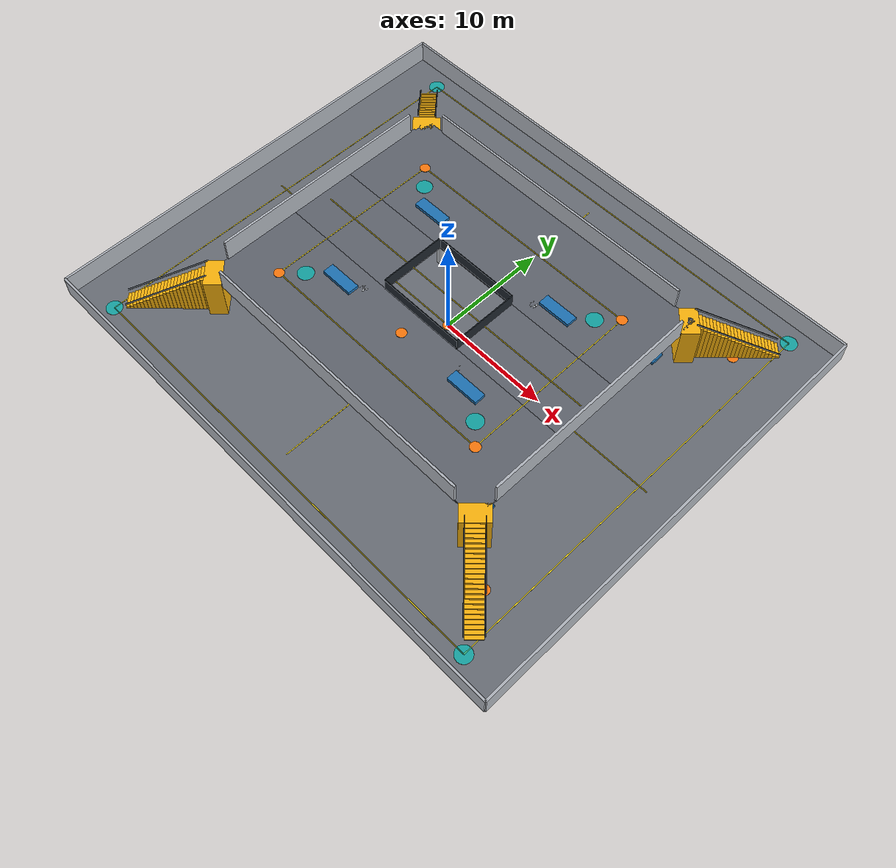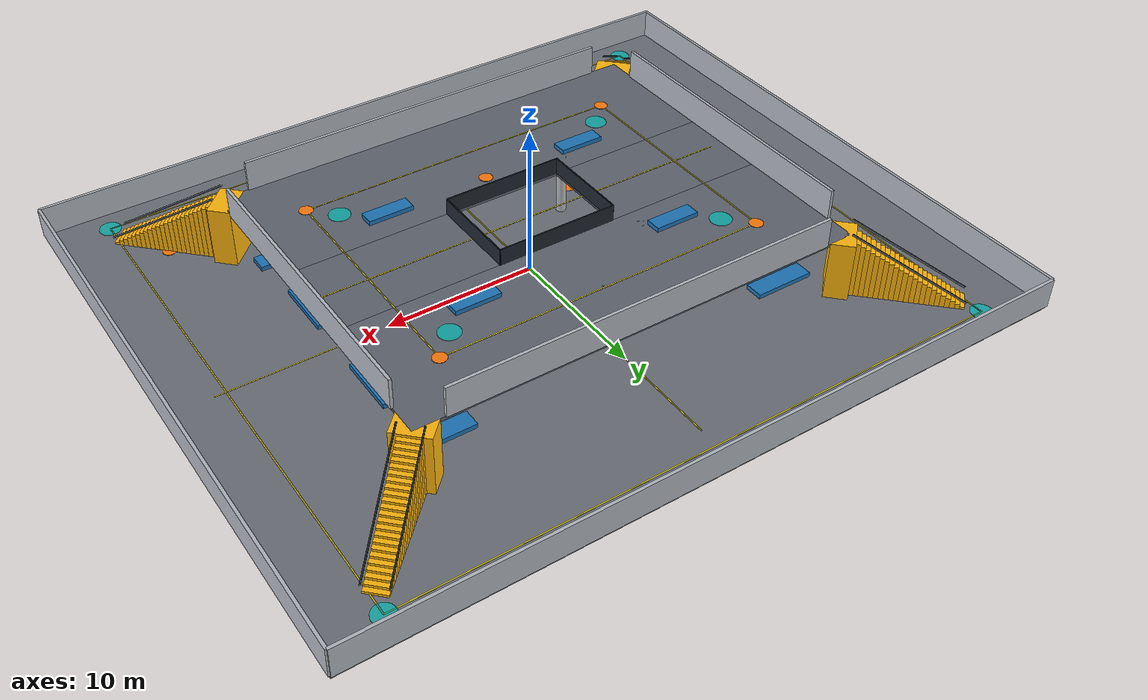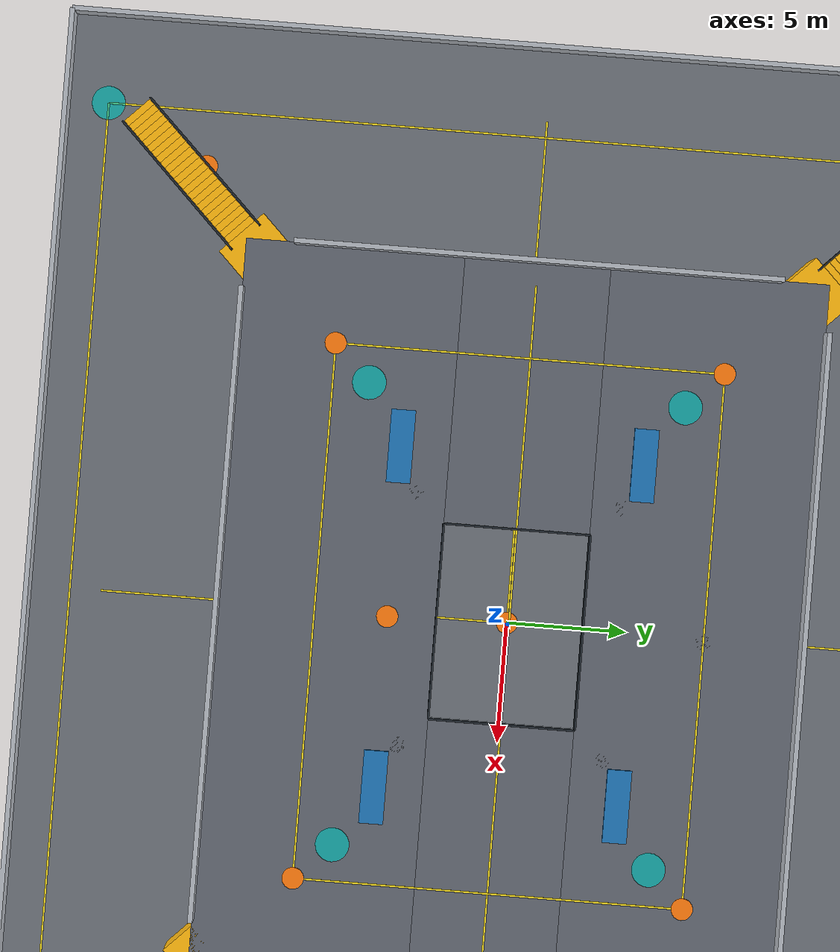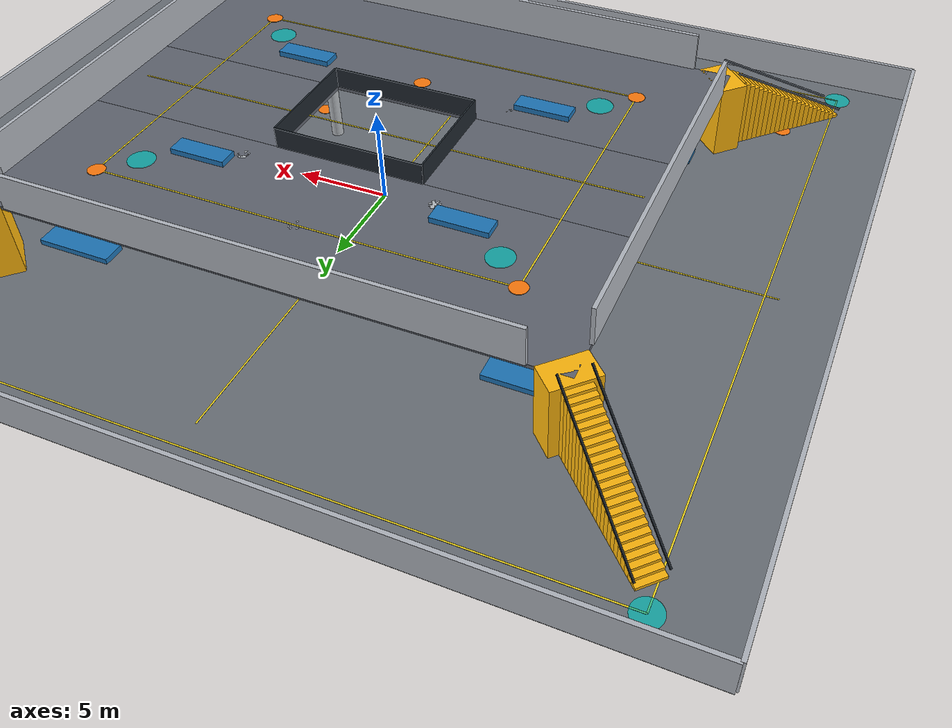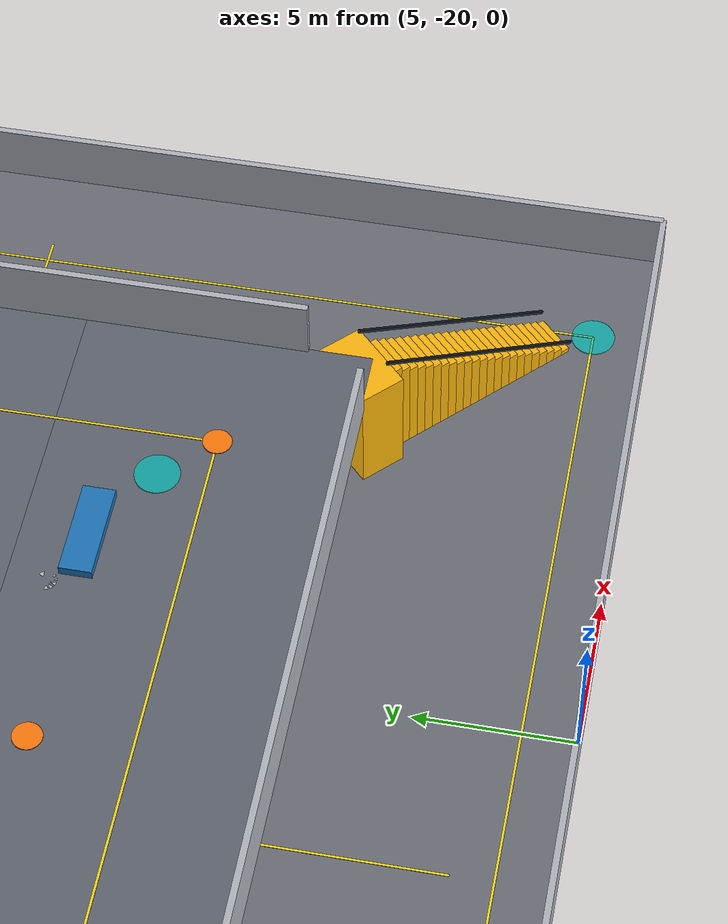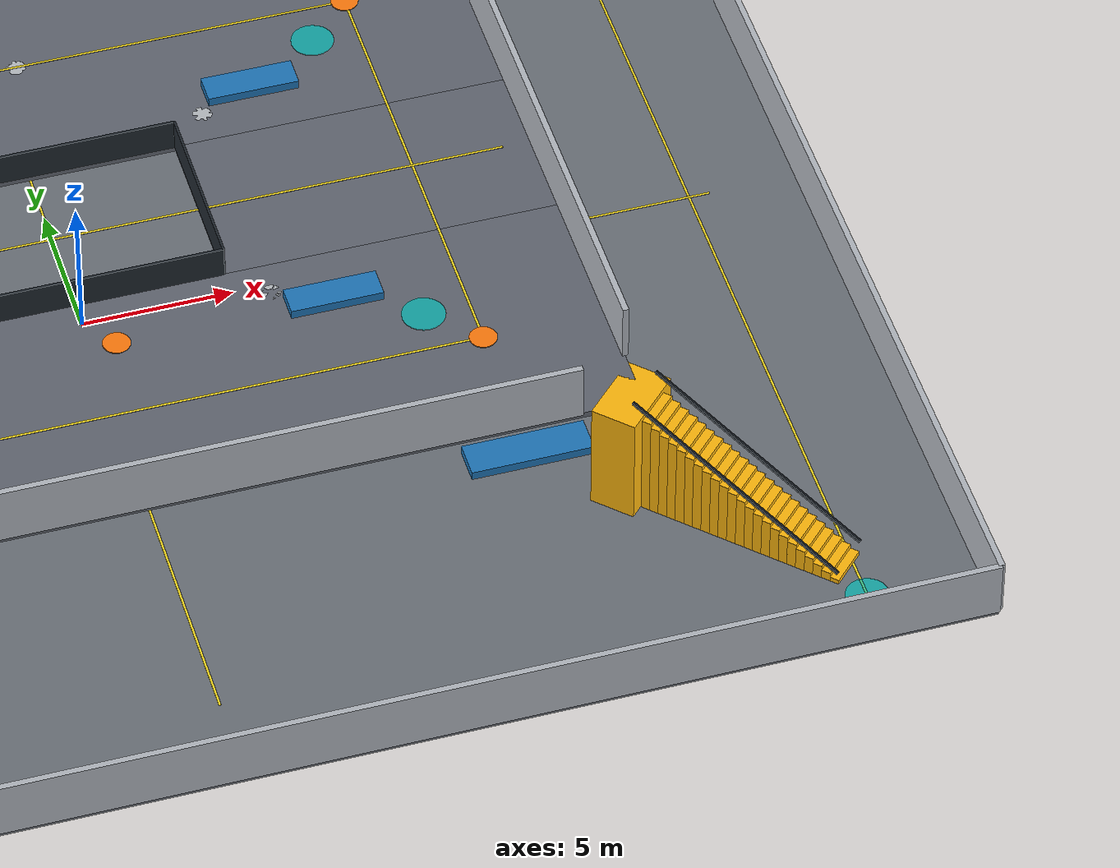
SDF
<sdf version="1.7">
 <world name="two_floor_warehouse">
  <physics name="default" type="ode">
   <max_step_size>0.01</max_step_size>
   <real_time_update_rate>1000</real_time_update_rate>
  </physics>
  <plugin filename="gz-sim-physics-system" name="gz::sim::systems::Physics"/>
  <plugin filename="gz-sim-user-commands-system" name="gz::sim::systems::UserCommands"/>
  <plugin filename="gz-sim-scene-broadcaster-system" name="gz::sim::systems::SceneBroadcaster"/>
  <plugin filename="gz-sim-sensors-system" name="gz::sim::systems::Sensors">
   <render_engine>ogre2</render_engine>
  </plugin>
  <plugin filename="gz-sim-imu-system" name="gz::sim::systems::Imu"/>
  <light name="sun" type="directional">
   <pose>0 0 30 0 0 0</pose>
   <diffuse>0.9 0.9 0.9 1</diffuse>
   <specular>0.25 0.25 0.25 1</specular>
   <direction>-0.35 0.25 -0.9</direction>
  </light>
  <model name="floor1">
   <static>true</static>
   <pose>0.0000 0.0000 -0.1000 0.0000 0.0000 0.0000</pose>
   <link name="link">
    <collision name="collision"><geometry><box><size>48 40 0.2</size></box></geometry></collision>
    <visual name="visual">
     <geometry><box><size>48 40 0.2</size></box></geometry>
     <material><ambient>.42 .44 .47 1</ambient><diffuse>.42 .44 .47 1</diffuse></material>
    </visual>
   </link>
  </model>
  <model name="floor2_north">
   <static>true</static>
   <pose>0.0000 7.5000 3.9000 0.0000 0.0000 0.0000</pose>
   <link name="link">
    <collision name="collision"><geometry><box><size>30.0 9.0 0.2</size></box></geometry></collision>
    <visual name="visual">
     <geometry><box><size>30.0 9.0 0.2</size></box></geometry>
     <material><ambient>.38 .40 .44 1</ambient><diffuse>.38 .40 .44 1</diffuse></material>
    </visual>
   </link>
  </model>
  <model name="floor2_south">
   <static>true</static>
   <pose>0.0000 -7.5000 3.9000 0.0000 0.0000 0.0000</pose>
   <link name="link">
    <collision name="collision"><geometry><box><size>30.0 9.0 0.2</size></box></geometry></collision>
    <visual name="visual">
     <geometry><box><size>30.0 9.0 0.2</size></box></geometry>
     <material><ambient>.38 .40 .44 1</ambient><diffuse>.38 .40 .44 1</diffuse></material>
    </visual>
   </link>
  </model>
  <model name="floor2_west">
   <static>true</static>
   <pose>-9.5000 0.0000 3.9000 0.0000 0.0000 0.0000</pose>
   <link name="link">
    <collision name="collision"><geometry><box><size>11.0 6.0 0.2</size></box></geometry></collision>
    <visual name="visual">
     <geometry><box><size>11.0 6.0 0.2</size></box></geometry>
     <material><ambient>.38 .40 .44 1</ambient><diffuse>.38 .40 .44 1</diffuse></material>
    </visual>
   </link>
  </model>
  <model name="floor2_east">
   <static>true</static>
   <pose>9.5000 0.0000 3.9000 0.0000 0.0000 0.0000</pose>
   <link name="link">
    <collision name="collision"><geometry><box><size>11.0 6.0 0.2</size></box></geometry></collision>
    <visual name="visual">
     <geometry><box><size>11.0 6.0 0.2</size></box></geometry>
     <material><ambient>.38 .40 .44 1</ambient><diffuse>.38 .40 .44 1</diffuse></material>
    </visual>
   </link>
  </model>
  <model name="atrium_rail_north">
   <static>true</static>
   <pose>0.0000 3.0000 4.5500 0.0000 0.0000 0.0000</pose>
   <link name="link">
    <collision name="collision"><geometry><box><size>8.0 0.08 1.1</size></box></geometry></collision>
    <visual name="visual">
     <geometry><box><size>8.0 0.08 1.1</size></box></geometry>
     <material><ambient>.12 .15 .18 1</ambient><diffuse>.12 .15 .18 1</diffuse></material>
    </visual>
   </link>
  </model>
  <model name="atrium_rail_south">
   <static>true</static>
   <pose>0.0000 -3.0000 4.5500 0.0000 0.0000 0.0000</pose>
   <link name="link">
    <collision name="collision"><geometry><box><size>8.0 0.08 1.1</size></box></geometry></collision>
    <visual name="visual">
     <geometry><box><size>8.0 0.08 1.1</size></box></geometry>
     <material><ambient>.12 .15 .18 1</ambient><diffuse>.12 .15 .18 1</diffuse></material>
    </visual>
   </link>
  </model>
  <model name="atrium_rail_west">
   <static>true</static>
   <pose>-4.0000 0.0000 4.5500 0.0000 0.0000 0.0000</pose>
   <link name="link">
    <collision name="collision"><geometry><box><size>0.08 6.0 1.1</size></box></geometry></collision>
    <visual name="visual">
     <geometry><box><size>0.08 6.0 1.1</size></box></geometry>
     <material><ambient>.12 .15 .18 1</ambient><diffuse>.12 .15 .18 1</diffuse></material>
    </visual>
   </link>
  </model>
  <model name="atrium_rail_east">
   <static>true</static>
   <pose>4.0000 0.0000 4.5500 0.0000 0.0000 0.0000</pose>
   <link name="link">
    <collision name="collision"><geometry><box><size>0.08 6.0 1.1</size></box></geometry></collision>
    <visual name="visual">
     <geometry><box><size>0.08 6.0 1.1</size></box></geometry>
     <material><ambient>.12 .15 .18 1</ambient><diffuse>.12 .15 .18 1</diffuse></material>
    </visual>
   </link>
  </model>
  <model name="f1_wall_n">
   <static>true</static>
   <pose>0.0000 20.0000 1.0000 0.0000 0.0000 0.0000</pose>
   <link name="link">
    <collision name="collision"><geometry><box><size>48.0 0.2 2</size></box></geometry></collision>
    <visual name="visual">
     <geometry><box><size>48.0 0.2 2</size></box></geometry>
     <material><ambient>.7 .72 .75 1</ambient><diffuse>.7 .72 .75 1</diffuse></material>
    </visual>
   </link>
  </model>
  <model name="f1_wall_s">
   <static>true</static>
   <pose>0.0000 -20.0000 1.0000 0.0000 0.0000 0.0000</pose>
   <link name="link">
    <collision name="collision"><geometry><box><size>48.0 0.2 2</size></box></geometry></collision>
    <visual name="visual">
     <geometry><box><size>48.0 0.2 2</size></box></geometry>
     <material><ambient>.7 .72 .75 1</ambient><diffuse>.7 .72 .75 1</diffuse></material>
    </visual>
   </link>
  </model>
  <model name="f1_wall_e">
   <static>true</static>
   <pose>24.0000 0.0000 1.0000 0.0000 0.0000 0.0000</pose>
   <link name="link">
    <collision name="collision"><geometry><box><size>0.2 40.0 2</size></box></geometry></collision>
    <visual name="visual">
     <geometry><box><size>0.2 40.0 2</size></box></geometry>
     <material><ambient>.7 .72 .75 1</ambient><diffuse>.7 .72 .75 1</diffuse></material>
    </visual>
   </link>
  </model>
  <model name="f1_wall_w">
   <static>true</static>
   <pose>-24.0000 0.0000 1.0000 0.0000 0.0000 0.0000</pose>
   <link name="link">
    <collision name="collision"><geometry><box><size>0.2 40.0 2</size></box></geometry></collision>
    <visual name="visual">
     <geometry><box><size>0.2 40.0 2</size></box></geometry>
     <material><ambient>.7 .72 .75 1</ambient><diffuse>.7 .72 .75 1</diffuse></material>
    </visual>
   </link>
  </model>
  <model name="f2_wall_n">
   <static>true</static>
   <pose>0.0000 12.0000 5.0000 0.0000 0.0000 0.0000</pose>
   <link name="link">
    <collision name="collision"><geometry><box><size>26.0 0.2 2</size></box></geometry></collision>
    <visual name="visual">
     <geometry><box><size>26.0 0.2 2</size></box></geometry>
     <material><ambient>.7 .72 .75 1</ambient><diffuse>.7 .72 .75 1</diffuse></material>
    </visual>
   </link>
  </model>
  <model name="f2_wall_s">
   <static>true</static>
   <pose>0.0000 -12.0000 5.0000 0.0000 0.0000 0.0000</pose>
   <link name="link">
    <collision name="collision"><geometry><box><size>26.0 0.2 2</size></box></geometry></collision>
    <visual name="visual">
     <geometry><box><size>26.0 0.2 2</size></box></geometry>
     <material><ambient>.7 .72 .75 1</ambient><diffuse>.7 .72 .75 1</diffuse></material>
    </visual>
   </link>
  </model>
  <model name="f2_wall_e">
   <static>true</static>
   <pose>15.0000 0.0000 5.0000 0.0000 0.0000 0.0000</pose>
   <link name="link">
    <collision name="collision"><geometry><box><size>0.2 20.0 2</size></box></geometry></collision>
    <visual name="visual">
     <geometry><box><size>0.2 20.0 2</size></box></geometry>
     <material><ambient>.7 .72 .75 1</ambient><diffuse>.7 .72 .75 1</diffuse></material>
    </visual>
   </link>
  </model>
  <model name="f2_wall_w">
   <static>true</static>
   <pose>-15.0000 0.0000 5.0000 0.0000 0.0000 0.0000</pose>
   <link name="link">
    <collision name="collision"><geometry><box><size>0.2 20.0 2</size></box></geometry></collision>
    <visual name="visual">
     <geometry><box><size>0.2 20.0 2</size></box></geometry>
     <material><ambient>.7 .72 .75 1</ambient><diffuse>.7 .72 .75 1</diffuse></material>
    </visual>
   </link>
  </model>
  <model name="stair_ne">
   <static>true</static>
   <link name="step_01">
    <pose>19.9849 16.9849 0.0833 0 0 -2.356194</pose>
    <collision name="collision"><geometry><box><size>0.3080 1.4000 0.1667</size></box></geometry></collision>
    <visual name="visual">
     <geometry><box><size>0.3080 1.4000 0.1667</size></box></geometry>
     <material><ambient>1.0 0.72 0.05 1</ambient><diffuse>1.0 0.72 0.05 1</diffuse></material>
    </visual>
   </link>
   <link name="step_02">
    <pose>19.7728 16.7728 0.1667 0 0 -2.356194</pose>
    <collision name="collision"><geometry><box><size>0.3080 1.4000 0.3333</size></box></geometry></collision>
    <visual name="visual">
     <geometry><box><size>0.3080 1.4000 0.3333</size></box></geometry>
     <material><ambient>1.0 0.72 0.05 1</ambient><diffuse>1.0 0.72 0.05 1</diffuse></material>
    </visual>
   </link>
   <link name="step_03">
    <pose>19.5607 16.5607 0.2500 0 0 -2.356194</pose>
    <collision name="collision"><geometry><box><size>0.3080 1.4000 0.5000</size></box></geometry></collision>
    <visual name="visual">
     <geometry><box><size>0.3080 1.4000 0.5000</size></box></geometry>
     <material><ambient>1.0 0.72 0.05 1</ambient><diffuse>1.0 0.72 0.05 1</diffuse></material>
    </visual>
   </link>
   <link name="step_04">
    <pose>19.3486 16.3486 0.3333 0 0 -2.356194</pose>
    <collision name="collision"><geometry><box><size>0.3080 1.4000 0.6667</size></box></geometry></collision>
    <visual name="visual">
     <geometry><box><size>0.3080 1.4000 0.6667</size></box></geometry>
     <material><ambient>1.0 0.72 0.05 1</ambient><diffuse>1.0 0.72 0.05 1</diffuse></material>
    </visual>
   </link>
   <link name="step_05">
    <pose>19.1364 16.1364 0.4167 0 0 -2.356194</pose>
    <collision name="collision"><geometry><box><size>0.3080 1.4000 0.8333</size></box></geometry></collision>
    <visual name="visual">
     <geometry><box><size>0.3080 1.4000 0.8333</size></box></geometry>
     <material><ambient>1.0 0.72 0.05 1</ambient><diffuse>1.0 0.72 0.05 1</diffuse></material>
    </visual>
   </link>
   <link name="step_06">
    <pose>18.9243 15.9243 0.5000 0 0 -2.356194</pose>
    <collision name="collision"><geometry><box><size>0.3080 1.4000 1.0000</size></box></geometry></collision>
    <visual name="visual">
     <geometry><box><size>0.3080 1.4000 1.0000</size></box></geometry>
     <material><ambient>1.0 0.72 0.05 1</ambient><diffuse>1.0 0.72 0.05 1</diffuse></material>
    </visual>
   </link>
   <link name="step_07">
    <pose>18.7122 15.7122 0.5833 0 0 -2.356194</pose>
    <collision name="collision"><geometry><box><size>0.3080 1.4000 1.1667</size></box></geometry></collision>
    <visual name="visual">
     <geometry><box><size>0.3080 1.4000 1.1667</size></box></geometry>
     <material><ambient>1.0 0.72 0.05 1</ambient><diffuse>1.0 0.72 0.05 1</diffuse></material>
    </visual>
   </link>
   <link name="step_08">
    <pose>18.5001 15.5001 0.6667 0 0 -2.356194</pose>
    <collision name="collision"><geometry><box><size>0.3080 1.4000 1.3333</size></box></geometry></collision>
    <visual name="visual">
     <geometry><box><size>0.3080 1.4000 1.3333</size></box></geometry>
     <material><ambient>1.0 0.72 0.05 1</ambient><diffuse>1.0 0.72 0.05 1</diffuse></material>
    </visual>
   </link>
   <link name="step_09">
    <pose>18.2879 15.2879 0.7500 0 0 -2.356194</pose>
    <collision name="collision"><geometry><box><size>0.3080 1.4000 1.5000</size></box></geometry></collision>
    <visual name="visual">
     <geometry><box><size>0.3080 1.4000 1.5000</size></box></geometry>
     <material><ambient>1.0 0.72 0.05 1</ambient><diffuse>1.0 0.72 0.05 1</diffuse></material>
    </visual>
   </link>
   <link name="step_10">
    <pose>18.0758 15.0758 0.8333 0 0 -2.356194</pose>
    <collision name="collision"><geometry><box><size>0.3080 1.4000 1.6667</size></box></geometry></collision>
    <visual name="visual">
     <geometry><box><size>0.3080 1.4000 1.6667</size></box></geometry>
     <material><ambient>1.0 0.72 0.05 1</ambient><diffuse>1.0 0.72 0.05 1</diffuse></material>
    </visual>
   </link>
   <link name="step_11">
    <pose>17.8637 14.8637 0.9167 0 0 -2.356194</pose>
    <collision name="collision"><geometry><box><size>0.3080 1.4000 1.8333</size></box></geometry></collision>
    <visual name="visual">
     <geometry><box><size>0.3080 1.4000 1.8333</size></box></geometry>
     <material><ambient>1.0 0.72 0.05 1</ambient><diffuse>1.0 0.72 0.05 1</diffuse></material>
    </visual>
   </link>
   <link name="step_12">
    <pose>17.6516 14.6516 1.0000 0 0 -2.356194</pose>
    <collision name="collision"><geometry><box><size>0.3080 1.4000 2.0000</size></box></geometry></collision>
    <visual name="visual">
     <geometry><box><size>0.3080 1.4000 2.0000</size></box></geometry>
     <material><ambient>1.0 0.72 0.05 1</ambient><diffuse>1.0 0.72 0.05 1</diffuse></material>
    </visual>
   </link>
   <link name="step_13">
    <pose>17.4394 14.4394 1.0833 0 0 -2.356194</pose>
    <collision name="collision"><geometry><box><size>0.3080 1.4000 2.1667</size></box></geometry></collision>
    <visual name="visual">
     <geometry><box><size>0.3080 1.4000 2.1667</size></box></geometry>
     <material><ambient>1.0 0.72 0.05 1</ambient><diffuse>1.0 0.72 0.05 1</diffuse></material>
    </visual>
   </link>
   <link name="step_14">
    <pose>17.2273 14.2273 1.1667 0 0 -2.356194</pose>
    <collision name="collision"><geometry><box><size>0.3080 1.4000 2.3333</size></box></geometry></collision>
    <visual name="visual">
     <geometry><box><size>0.3080 1.4000 2.3333</size></box></geometry>
     <material><ambient>1.0 0.72 0.05 1</ambient><diffuse>1.0 0.72 0.05 1</diffuse></material>
    </visual>
   </link>
   <link name="step_15">
    <pose>17.0152 14.0152 1.2500 0 0 -2.356194</pose>
    <collision name="collision"><geometry><box><size>0.3080 1.4000 2.5000</size></box></geometry></collision>
    <visual name="visual">
     <geometry><box><size>0.3080 1.4000 2.5000</size></box></geometry>
     <material><ambient>1.0 0.72 0.05 1</ambient><diffuse>1.0 0.72 0.05 1</diffuse></material>
    </visual>
   </link>
   <link name="step_16">
    <pose>16.8031 13.8031 1.3333 0 0 -2.356194</pose>
    <collision name="collision"><geometry><box><size>0.3080 1.4000 2.6667</size></box></geometry></collision>
    <visual name="visual">
     <geometry><box><size>0.3080 1.4000 2.6667</size></box></geometry>
     <material><ambient>1.0 0.72 0.05 1</ambient><diffuse>1.0 0.72 0.05 1</diffuse></material>
    </visual>
   </link>
   <link name="step_17">
    <pose>16.5909 13.5909 1.4167 0 0 -2.356194</pose>
    <collision name="collision"><geometry><box><size>0.3080 1.4000 2.8333</size></box></geometry></collision>
    <visual name="visual">
     <geometry><box><size>0.3080 1.4000 2.8333</size></box></geometry>
     <material><ambient>1.0 0.72 0.05 1</ambient><diffuse>1.0 0.72 0.05 1</diffuse></material>
    </visual>
   </link>
   <link name="step_18">
    <pose>16.3788 13.3788 1.5000 0 0 -2.356194</pose>
    <collision name="collision"><geometry><box><size>0.3080 1.4000 3.0000</size></box></geometry></collision>
    <visual name="visual">
     <geometry><box><size>0.3080 1.4000 3.0000</size></box></geometry>
     <material><ambient>1.0 0.72 0.05 1</ambient><diffuse>1.0 0.72 0.05 1</diffuse></material>
    </visual>
   </link>
   <link name="step_19">
    <pose>16.1667 13.1667 1.5833 0 0 -2.356194</pose>
    <collision name="collision"><geometry><box><size>0.3080 1.4000 3.1667</size></box></geometry></collision>
    <visual name="visual">
     <geometry><box><size>0.3080 1.4000 3.1667</size></box></geometry>
     <material><ambient>1.0 0.72 0.05 1</ambient><diffuse>1.0 0.72 0.05 1</diffuse></material>
    </visual>
   </link>
   <link name="step_20">
    <pose>15.9546 12.9546 1.6667 0 0 -2.356194</pose>
    <collision name="collision"><geometry><box><size>0.3080 1.4000 3.3333</size></box></geometry></collision>
    <visual name="visual">
     <geometry><box><size>0.3080 1.4000 3.3333</size></box></geometry>
     <material><ambient>1.0 0.72 0.05 1</ambient><diffuse>1.0 0.72 0.05 1</diffuse></material>
    </visual>
   </link>
   <link name="step_21">
    <pose>15.7424 12.7424 1.7500 0 0 -2.356194</pose>
    <collision name="collision"><geometry><box><size>0.3080 1.4000 3.5000</size></box></geometry></collision>
    <visual name="visual">
     <geometry><box><size>0.3080 1.4000 3.5000</size></box></geometry>
     <material><ambient>1.0 0.72 0.05 1</ambient><diffuse>1.0 0.72 0.05 1</diffuse></material>
    </visual>
   </link>
   <link name="step_22">
    <pose>15.5303 12.5303 1.8333 0 0 -2.356194</pose>
    <collision name="collision"><geometry><box><size>0.3080 1.4000 3.6667</size></box></geometry></collision>
    <visual name="visual">
     <geometry><box><size>0.3080 1.4000 3.6667</size></box></geometry>
     <material><ambient>1.0 0.72 0.05 1</ambient><diffuse>1.0 0.72 0.05 1</diffuse></material>
    </visual>
   </link>
   <link name="step_23">
    <pose>15.3182 12.3182 1.9167 0 0 -2.356194</pose>
    <collision name="collision"><geometry><box><size>0.3080 1.4000 3.8333</size></box></geometry></collision>
    <visual name="visual">
     <geometry><box><size>0.3080 1.4000 3.8333</size></box></geometry>
     <material><ambient>1.0 0.72 0.05 1</ambient><diffuse>1.0 0.72 0.05 1</diffuse></material>
    </visual>
   </link>
   <link name="step_24">
    <pose>14.6818 11.6818 2.0000 0 0 -2.356194</pose>
    <collision name="collision"><geometry><box><size>1.5080 2.4000 4.0000</size></box></geometry></collision>
    <visual name="visual">
     <geometry><box><size>1.5080 2.4000 4.0000</size></box></geometry>
     <material><ambient>1.0 0.72 0.05 1</ambient><diffuse>1.0 0.72 0.05 1</diffuse></material>
    </visual>
   </link>
   <link name="rail_-1">
    <pose>17.0081 15.0829 2.55 0 -0.507113 -2.356194</pose>
    <collision name="collision"><geometry><box><size>8.2363 0.08 0.10</size></box></geometry></collision>
    <visual name="visual">
     <geometry><box><size>8.2363 0.08 0.10</size></box></geometry>
     <material><ambient>0.12 0.15 0.18 1</ambient></material>
    </visual>
   </link>
   <link name="rail_+1">
    <pose>18.0829 14.0081 2.55 0 -0.507113 -2.356194</pose>
    <collision name="collision"><geometry><box><size>8.2363 0.08 0.10</size></box></geometry></collision>
    <visual name="visual">
     <geometry><box><size>8.2363 0.08 0.10</size></box></geometry>
     <material><ambient>0.12 0.15 0.18 1</ambient></material>
    </visual>
   </link>
  </model>
  <model name="stair_nw">
   <static>true</static>
   <link name="step_01">
    <pose>-19.9849 16.9849 0.0833 0 0 -0.785398</pose>
    <collision name="collision"><geometry><box><size>0.3080 1.4000 0.1667</size></box></geometry></collision>
    <visual name="visual">
     <geometry><box><size>0.3080 1.4000 0.1667</size></box></geometry>
     <material><ambient>1.0 0.72 0.05 1</ambient><diffuse>1.0 0.72 0.05 1</diffuse></material>
    </visual>
   </link>
   <link name="step_02">
    <pose>-19.7728 16.7728 0.1667 0 0 -0.785398</pose>
    <collision name="collision"><geometry><box><size>0.3080 1.4000 0.3333</size></box></geometry></collision>
    <visual name="visual">
     <geometry><box><size>0.3080 1.4000 0.3333</size></box></geometry>
     <material><ambient>1.0 0.72 0.05 1</ambient><diffuse>1.0 0.72 0.05 1</diffuse></material>
    </visual>
   </link>
   <link name="step_03">
    <pose>-19.5607 16.5607 0.2500 0 0 -0.785398</pose>
    <collision name="collision"><geometry><box><size>0.3080 1.4000 0.5000</size></box></geometry></collision>
    <visual name="visual">
     <geometry><box><size>0.3080 1.4000 0.5000</size></box></geometry>
     <material><ambient>1.0 0.72 0.05 1</ambient><diffuse>1.0 0.72 0.05 1</diffuse></material>
    </visual>
   </link>
   <link name="step_04">
    <pose>-19.3486 16.3486 0.3333 0 0 -0.785398</pose>
    <collision name="collision"><geometry><box><size>0.3080 1.4000 0.6667</size></box></geometry></collision>
    <visual name="visual">
     <geometry><box><size>0.3080 1.4000 0.6667</size></box></geometry>
     <material><ambient>1.0 0.72 0.05 1</ambient><diffuse>1.0 0.72 0.05 1</diffuse></material>
    </visual>
   </link>
   <link name="step_05">
    <pose>-19.1364 16.1364 0.4167 0 0 -0.785398</pose>
    <collision name="collision"><geometry><box><size>0.3080 1.4000 0.8333</size></box></geometry></collision>
    <visual name="visual">
     <geometry><box><size>0.3080 1.4000 0.8333</size></box></geometry>
     <material><ambient>1.0 0.72 0.05 1</ambient><diffuse>1.0 0.72 0.05 1</diffuse></material>
    </visual>
   </link>
   <link name="step_06">
    <pose>-18.9243 15.9243 0.5000 0 0 -0.785398</pose>
    <collision name="collision"><geometry><box><size>0.3080 1.4000 1.0000</size></box></geometry></collision>
    <visual name="visual">
     <geometry><box><size>0.3080 1.4000 1.0000</size></box></geometry>
     <material><ambient>1.0 0.72 0.05 1</ambient><diffuse>1.0 0.72 0.05 1</diffuse></material>
    </visual>
   </link>
   <link name="step_07">
    <pose>-18.7122 15.7122 0.5833 0 0 -0.785398</pose>
    <collision name="collision"><geometry><box><size>0.3080 1.4000 1.1667</size></box></geometry></collision>
    <visual name="visual">
     <geometry><box><size>0.3080 1.4000 1.1667</size></box></geometry>
     <material><ambient>1.0 0.72 0.05 1</ambient><diffuse>1.0 0.72 0.05 1</diffuse></material>
    </visual>
   </link>
   <link name="step_08">
    <pose>-18.5001 15.5001 0.6667 0 0 -0.785398</pose>
    <collision name="collision"><geometry><box><size>0.3080 1.4000 1.3333</size></box></geometry></collision>
    <visual name="visual">
     <geometry><box><size>0.3080 1.4000 1.3333</size></box></geometry>
     <material><ambient>1.0 0.72 0.05 1</ambient><diffuse>1.0 0.72 0.05 1</diffuse></material>
    </visual>
   </link>
   <link name="step_09">
    <pose>-18.2879 15.2879 0.7500 0 0 -0.785398</pose>
    <collision name="collision"><geometry><box><size>0.3080 1.4000 1.5000</size></box></geometry></collision>
    <visual name="visual">
     <geometry><box><size>0.3080 1.4000 1.5000</size></box></geometry>
     <material><ambient>1.0 0.72 0.05 1</ambient><diffuse>1.0 0.72 0.05 1</diffuse></material>
    </visual>
   </link>
   <link name="step_10">
    <pose>-18.0758 15.0758 0.8333 0 0 -0.785398</pose>
    <collision name="collision"><geometry><box><size>0.3080 1.4000 1.6667</size></box></geometry></collision>
    <visual name="visual">
     <geometry><box><size>0.3080 1.4000 1.6667</size></box></geometry>
     <material><ambient>1.0 0.72 0.05 1</ambient><diffuse>1.0 0.72 0.05 1</diffuse></material>
    </visual>
   </link>
   <link name="step_11">
    <pose>-17.8637 14.8637 0.9167 0 0 -0.785398</pose>
    <collision name="collision"><geometry><box><size>0.3080 1.4000 1.8333</size></box></geometry></collision>
    <visual name="visual">
     <geometry><box><size>0.3080 1.4000 1.8333</size></box></geometry>
     <material><ambient>1.0 0.72 0.05 1</ambient><diffuse>1.0 0.72 0.05 1</diffuse></material>
    </visual>
   </link>
   <link name="step_12">
    <pose>-17.6516 14.6516 1.0000 0 0 -0.785398</pose>
    <collision name="collision"><geometry><box><size>0.3080 1.4000 2.0000</size></box></geometry></collision>
    <visual name="visual">
     <geometry><box><size>0.3080 1.4000 2.0000</size></box></geometry>
     <material><ambient>1.0 0.72 0.05 1</ambient><diffuse>1.0 0.72 0.05 1</diffuse></material>
    </visual>
   </link>
   <link name="step_13">
    <pose>-17.4394 14.4394 1.0833 0 0 -0.785398</pose>
    <collision name="collision"><geometry><box><size>0.3080 1.4000 2.1667</size></box></geometry></collision>
    <visual name="visual">
     <geometry><box><size>0.3080 1.4000 2.1667</size></box></geometry>
     <material><ambient>1.0 0.72 0.05 1</ambient><diffuse>1.0 0.72 0.05 1</diffuse></material>
    </visual>
   </link>
   <link name="step_14">
    <pose>-17.2273 14.2273 1.1667 0 0 -0.785398</pose>
    <collision name="collision"><geometry><box><size>0.3080 1.4000 2.3333</size></box></geometry></collision>
    <visual name="visual">
     <geometry><box><size>0.3080 1.4000 2.3333</size></box></geometry>
     <material><ambient>1.0 0.72 0.05 1</ambient><diffuse>1.0 0.72 0.05 1</diffuse></material>
    </visual>
   </link>
   <link name="step_15">
    <pose>-17.0152 14.0152 1.2500 0 0 -0.785398</pose>
    <collision name="collision"><geometry><box><size>0.3080 1.4000 2.5000</size></box></geometry></collision>
    <visual name="visual">
     <geometry><box><size>0.3080 1.4000 2.5000</size></box></geometry>
     <material><ambient>1.0 0.72 0.05 1</ambient><diffuse>1.0 0.72 0.05 1</diffuse></material>
    </visual>
   </link>
   <link name="step_16">
    <pose>-16.8031 13.8031 1.3333 0 0 -0.785398</pose>
    <collision name="collision"><geometry><box><size>0.3080 1.4000 2.6667</size></box></geometry></collision>
    <visual name="visual">
     <geometry><box><size>0.3080 1.4000 2.6667</size></box></geometry>
     <material><ambient>1.0 0.72 0.05 1</ambient><diffuse>1.0 0.72 0.05 1</diffuse></material>
    </visual>
   </link>
   <link name="step_17">
    <pose>-16.5909 13.5909 1.4167 0 0 -0.785398</pose>
    <collision name="collision"><geometry><box><size>0.3080 1.4000 2.8333</size></box></geometry></collision>
    <visual name="visual">
     <geometry><box><size>0.3080 1.4000 2.8333</size></box></geometry>
     <material><ambient>1.0 0.72 0.05 1</ambient><diffuse>1.0 0.72 0.05 1</diffuse></material>
    </visual>
   </link>
   <link name="step_18">
    <pose>-16.3788 13.3788 1.5000 0 0 -0.785398</pose>
    <collision name="collision"><geometry><box><size>0.3080 1.4000 3.0000</size></box></geometry></collision>
    <visual name="visual">
     <geometry><box><size>0.3080 1.4000 3.0000</size></box></geometry>
     <material><ambient>1.0 0.72 0.05 1</ambient><diffuse>1.0 0.72 0.05 1</diffuse></material>
    </visual>
   </link>
   <link name="step_19">
    <pose>-16.1667 13.1667 1.5833 0 0 -0.785398</pose>
    <collision name="collision"><geometry><box><size>0.3080 1.4000 3.1667</size></box></geometry></collision>
    <visual name="visual">
     <geometry><box><size>0.3080 1.4000 3.1667</size></box></geometry>
     <material><ambient>1.0 0.72 0.05 1</ambient><diffuse>1.0 0.72 0.05 1</diffuse></material>
    </visual>
   </link>
   <link name="step_20">
    <pose>-15.9546 12.9546 1.6667 0 0 -0.785398</pose>
    <collision name="collision"><geometry><box><size>0.3080 1.4000 3.3333</size></box></geometry></collision>
    <visual name="visual">
     <geometry><box><size>0.3080 1.4000 3.3333</size></box></geometry>
     <material><ambient>1.0 0.72 0.05 1</ambient><diffuse>1.0 0.72 0.05 1</diffuse></material>
    </visual>
   </link>
   <link name="step_21">
    <pose>-15.7424 12.7424 1.7500 0 0 -0.785398</pose>
    <collision name="collision"><geometry><box><size>0.3080 1.4000 3.5000</size></box></geometry></collision>
    <visual name="visual">
     <geometry><box><size>0.3080 1.4000 3.5000</size></box></geometry>
     <material><ambient>1.0 0.72 0.05 1</ambient><diffuse>1.0 0.72 0.05 1</diffuse></material>
    </visual>
   </link>
   <link name="step_22">
    <pose>-15.5303 12.5303 1.8333 0 0 -0.785398</pose>
    <collision name="collision"><geometry><box><size>0.3080 1.4000 3.6667</size></box></geometry></collision>
    <visual name="visual">
     <geometry><box><size>0.3080 1.4000 3.6667</size></box></geometry>
     <material><ambient>1.0 0.72 0.05 1</ambient><diffuse>1.0 0.72 0.05 1</diffuse></material>
    </visual>
   </link>
   <link name="step_23">
    <pose>-15.3182 12.3182 1.9167 0 0 -0.785398</pose>
    <collision name="collision"><geometry><box><size>0.3080 1.4000 3.8333</size></box></geometry></collision>
    <visual name="visual">
     <geometry><box><size>0.3080 1.4000 3.8333</size></box></geometry>
     <material><ambient>1.0 0.72 0.05 1</ambient><diffuse>1.0 0.72 0.05 1</diffuse></material>
    </visual>
   </link>
   <link name="step_24">
    <pose>-14.6818 11.6818 2.0000 0 0 -0.785398</pose>
    <collision name="collision"><geometry><box><size>1.5080 2.4000 4.0000</size></box></geometry></collision>
    <visual name="visual">
     <geometry><box><size>1.5080 2.4000 4.0000</size></box></geometry>
     <material><ambient>1.0 0.72 0.05 1</ambient><diffuse>1.0 0.72 0.05 1</diffuse></material>
    </visual>
   </link>
   <link name="rail_-1">
    <pose>-18.0829 14.0081 2.55 0 -0.507113 -0.785398</pose>
    <collision name="collision"><geometry><box><size>8.2363 0.08 0.10</size></box></geometry></collision>
    <visual name="visual">
     <geometry><box><size>8.2363 0.08 0.10</size></box></geometry>
     <material><ambient>0.12 0.15 0.18 1</ambient></material>
    </visual>
   </link>
   <link name="rail_+1">
    <pose>-17.0081 15.0829 2.55 0 -0.507113 -0.785398</pose>
    <collision name="collision"><geometry><box><size>8.2363 0.08 0.10</size></box></geometry></collision>
    <visual name="visual">
     <geometry><box><size>8.2363 0.08 0.10</size></box></geometry>
     <material><ambient>0.12 0.15 0.18 1</ambient></material>
    </visual>
   </link>
  </model>
  <model name="stair_sw">
   <static>true</static>
   <link name="step_01">
    <pose>-19.9849 -16.9849 0.0833 0 0 0.785398</pose>
    <collision name="collision"><geometry><box><size>0.3080 1.4000 0.1667</size></box></geometry></collision>
    <visual name="visual">
     <geometry><box><size>0.3080 1.4000 0.1667</size></box></geometry>
     <material><ambient>1.0 0.72 0.05 1</ambient><diffuse>1.0 0.72 0.05 1</diffuse></material>
    </visual>
   </link>
   <link name="step_02">
    <pose>-19.7728 -16.7728 0.1667 0 0 0.785398</pose>
    <collision name="collision"><geometry><box><size>0.3080 1.4000 0.3333</size></box></geometry></collision>
    <visual name="visual">
     <geometry><box><size>0.3080 1.4000 0.3333</size></box></geometry>
     <material><ambient>1.0 0.72 0.05 1</ambient><diffuse>1.0 0.72 0.05 1</diffuse></material>
    </visual>
   </link>
   <link name="step_03">
    <pose>-19.5607 -16.5607 0.2500 0 0 0.785398</pose>
    <collision name="collision"><geometry><box><size>0.3080 1.4000 0.5000</size></box></geometry></collision>
    <visual name="visual">
     <geometry><box><size>0.3080 1.4000 0.5000</size></box></geometry>
     <material><ambient>1.0 0.72 0.05 1</ambient><diffuse>1.0 0.72 0.05 1</diffuse></material>
    </visual>
   </link>
   <link name="step_04">
    <pose>-19.3486 -16.3486 0.3333 0 0 0.785398</pose>
    <collision name="collision"><geometry><box><size>0.3080 1.4000 0.6667</size></box></geometry></collision>
    <visual name="visual">
     <geometry><box><size>0.3080 1.4000 0.6667</size></box></geometry>
     <material><ambient>1.0 0.72 0.05 1</ambient><diffuse>1.0 0.72 0.05 1</diffuse></material>
    </visual>
   </link>
   <link name="step_05">
    <pose>-19.1364 -16.1364 0.4167 0 0 0.785398</pose>
    <collision name="collision"><geometry><box><size>0.3080 1.4000 0.8333</size></box></geometry></collision>
    <visual name="visual">
     <geometry><box><size>0.3080 1.4000 0.8333</size></box></geometry>
     <material><ambient>1.0 0.72 0.05 1</ambient><diffuse>1.0 0.72 0.05 1</diffuse></material>
    </visual>
   </link>
   <link name="step_06">
    <pose>-18.9243 -15.9243 0.5000 0 0 0.785398</pose>
    <collision name="collision"><geometry><box><size>0.3080 1.4000 1.0000</size></box></geometry></collision>
    <visual name="visual">
     <geometry><box><size>0.3080 1.4000 1.0000</size></box></geometry>
     <material><ambient>1.0 0.72 0.05 1</ambient><diffuse>1.0 0.72 0.05 1</diffuse></material>
    </visual>
   </link>
   <link name="step_07">
    <pose>-18.7122 -15.7122 0.5833 0 0 0.785398</pose>
    <collision name="collision"><geometry><box><size>0.3080 1.4000 1.1667</size></box></geometry></collision>
    <visual name="visual">
     <geometry><box><size>0.3080 1.4000 1.1667</size></box></geometry>
     <material><ambient>1.0 0.72 0.05 1</ambient><diffuse>1.0 0.72 0.05 1</diffuse></material>
    </visual>
   </link>
   <link name="step_08">
    <pose>-18.5001 -15.5001 0.6667 0 0 0.785398</pose>
    <collision name="collision"><geometry><box><size>0.3080 1.4000 1.3333</size></box></geometry></collision>
    <visual name="visual">
     <geometry><box><size>0.3080 1.4000 1.3333</size></box></geometry>
     <material><ambient>1.0 0.72 0.05 1</ambient><diffuse>1.0 0.72 0.05 1</diffuse></material>
    </visual>
   </link>
   <link name="step_09">
    <pose>-18.2879 -15.2879 0.7500 0 0 0.785398</pose>
    <collision name="collision"><geometry><box><size>0.3080 1.4000 1.5000</size></box></geometry></collision>
    <visual name="visual">
     <geometry><box><size>0.3080 1.4000 1.5000</size></box></geometry>
     <material><ambient>1.0 0.72 0.05 1</ambient><diffuse>1.0 0.72 0.05 1</diffuse></material>
    </visual>
   </link>
   <link name="step_10">
    <pose>-18.0758 -15.0758 0.8333 0 0 0.785398</pose>
    <collision name="collision"><geometry><box><size>0.3080 1.4000 1.6667</size></box></geometry></collision>
    <visual name="visual">
     <geometry><box><size>0.3080 1.4000 1.6667</size></box></geometry>
     <material><ambient>1.0 0.72 0.05 1</ambient><diffuse>1.0 0.72 0.05 1</diffuse></material>
    </visual>
   </link>
   <link name="step_11">
    <pose>-17.8637 -14.8637 0.9167 0 0 0.785398</pose>
    <collision name="collision"><geometry><box><size>0.3080 1.4000 1.8333</size></box></geometry></collision>
    <visual name="visual">
     <geometry><box><size>0.3080 1.4000 1.8333</size></box></geometry>
     <material><ambient>1.0 0.72 0.05 1</ambient><diffuse>1.0 0.72 0.05 1</diffuse></material>
    </visual>
   </link>
   <link name="step_12">
    <pose>-17.6516 -14.6516 1.0000 0 0 0.785398</pose>
    <collision name="collision"><geometry><box><size>0.3080 1.4000 2.0000</size></box></geometry></collision>
    <visual name="visual">
     <geometry><box><size>0.3080 1.4000 2.0000</size></box></geometry>
     <material><ambient>1.0 0.72 0.05 1</ambient><diffuse>1.0 0.72 0.05 1</diffuse></material>
    </visual>
   </link>
   <link name="step_13">
    <pose>-17.4394 -14.4394 1.0833 0 0 0.785398</pose>
    <collision name="collision"><geometry><box><size>0.3080 1.4000 2.1667</size></box></geometry></collision>
    <visual name="visual">
     <geometry><box><size>0.3080 1.4000 2.1667</size></box></geometry>
     <material><ambient>1.0 0.72 0.05 1</ambient><diffuse>1.0 0.72 0.05 1</diffuse></material>
    </visual>
   </link>
   <link name="step_14">
    <pose>-17.2273 -14.2273 1.1667 0 0 0.785398</pose>
    <collision name="collision"><geometry><box><size>0.3080 1.4000 2.3333</size></box></geometry></collision>
    <visual name="visual">
     <geometry><box><size>0.3080 1.4000 2.3333</size></box></geometry>
     <material><ambient>1.0 0.72 0.05 1</ambient><diffuse>1.0 0.72 0.05 1</diffuse></material>
    </visual>
   </link>
   <link name="step_15">
    <pose>-17.0152 -14.0152 1.2500 0 0 0.785398</pose>
    <collision name="collision"><geometry><box><size>0.3080 1.4000 2.5000</size></box></geometry></collision>
    <visual name="visual">
     <geometry><box><size>0.3080 1.4000 2.5000</size></box></geometry>
     <material><ambient>1.0 0.72 0.05 1</ambient><diffuse>1.0 0.72 0.05 1</diffuse></material>
    </visual>
   </link>
   <link name="step_16">
    <pose>-16.8031 -13.8031 1.3333 0 0 0.785398</pose>
    <collision name="collision"><geometry><box><size>0.3080 1.4000 2.6667</size></box></geometry></collision>
    <visual name="visual">
     <geometry><box><size>0.3080 1.4000 2.6667</size></box></geometry>
     <material><ambient>1.0 0.72 0.05 1</ambient><diffuse>1.0 0.72 0.05 1</diffuse></material>
    </visual>
   </link>
   <link name="step_17">
    <pose>-16.5909 -13.5909 1.4167 0 0 0.785398</pose>
    <collision name="collision"><geometry><box><size>0.3080 1.4000 2.8333</size></box></geometry></collision>
    <visual name="visual">
     <geometry><box><size>0.3080 1.4000 2.8333</size></box></geometry>
     <material><ambient>1.0 0.72 0.05 1</ambient><diffuse>1.0 0.72 0.05 1</diffuse></material>
    </visual>
   </link>
   <link name="step_18">
    <pose>-16.3788 -13.3788 1.5000 0 0 0.785398</pose>
    <collision name="collision"><geometry><box><size>0.3080 1.4000 3.0000</size></box></geometry></collision>
    <visual name="visual">
     <geometry><box><size>0.3080 1.4000 3.0000</size></box></geometry>
     <material><ambient>1.0 0.72 0.05 1</ambient><diffuse>1.0 0.72 0.05 1</diffuse></material>
    </visual>
   </link>
   <link name="step_19">
    <pose>-16.1667 -13.1667 1.5833 0 0 0.785398</pose>
    <collision name="collision"><geometry><box><size>0.3080 1.4000 3.1667</size></box></geometry></collision>
    <visual name="visual">
     <geometry><box><size>0.3080 1.4000 3.1667</size></box></geometry>
     <material><ambient>1.0 0.72 0.05 1</ambient><diffuse>1.0 0.72 0.05 1</diffuse></material>
    </visual>
   </link>
   <link name="step_20">
    <pose>-15.9546 -12.9546 1.6667 0 0 0.785398</pose>
    <collision name="collision"><geometry><box><size>0.3080 1.4000 3.3333</size></box></geometry></collision>
    <visual name="visual">
     <geometry><box><size>0.3080 1.4000 3.3333</size></box></geometry>
     <material><ambient>1.0 0.72 0.05 1</ambient><diffuse>1.0 0.72 0.05 1</diffuse></material>
    </visual>
   </link>
   <link name="step_21">
    <pose>-15.7424 -12.7424 1.7500 0 0 0.785398</pose>
    <collision name="collision"><geometry><box><size>0.3080 1.4000 3.5000</size></box></geometry></collision>
    <visual name="visual">
     <geometry><box><size>0.3080 1.4000 3.5000</size></box></geometry>
     <material><ambient>1.0 0.72 0.05 1</ambient><diffuse>1.0 0.72 0.05 1</diffuse></material>
    </visual>
   </link>
   <link name="step_22">
    <pose>-15.5303 -12.5303 1.8333 0 0 0.785398</pose>
    <collision name="collision"><geometry><box><size>0.3080 1.4000 3.6667</size></box></geometry></collision>
    <visual name="visual">
     <geometry><box><size>0.3080 1.4000 3.6667</size></box></geometry>
     <material><ambient>1.0 0.72 0.05 1</ambient><diffuse>1.0 0.72 0.05 1</diffuse></material>
    </visual>
   </link>
   <link name="step_23">
    <pose>-15.3182 -12.3182 1.9167 0 0 0.785398</pose>
    <collision name="collision"><geometry><box><size>0.3080 1.4000 3.8333</size></box></geometry></collision>
    <visual name="visual">
     <geometry><box><size>0.3080 1.4000 3.8333</size></box></geometry>
     <material><ambient>1.0 0.72 0.05 1</ambient><diffuse>1.0 0.72 0.05 1</diffuse></material>
    </visual>
   </link>
   <link name="step_24">
    <pose>-14.6818 -11.6818 2.0000 0 0 0.785398</pose>
    <collision name="collision"><geometry><box><size>1.5080 2.4000 4.0000</size></box></geometry></collision>
    <visual name="visual">
     <geometry><box><size>1.5080 2.4000 4.0000</size></box></geometry>
     <material><ambient>1.0 0.72 0.05 1</ambient><diffuse>1.0 0.72 0.05 1</diffuse></material>
    </visual>
   </link>
   <link name="rail_-1">
    <pose>-17.0081 -15.0829 2.55 0 -0.507113 0.785398</pose>
    <collision name="collision"><geometry><box><size>8.2363 0.08 0.10</size></box></geometry></collision>
    <visual name="visual">
     <geometry><box><size>8.2363 0.08 0.10</size></box></geometry>
     <material><ambient>0.12 0.15 0.18 1</ambient></material>
    </visual>
   </link>
   <link name="rail_+1">
    <pose>-18.0829 -14.0081 2.55 0 -0.507113 0.785398</pose>
    <collision name="collision"><geometry><box><size>8.2363 0.08 0.10</size></box></geometry></collision>
    <visual name="visual">
     <geometry><box><size>8.2363 0.08 0.10</size></box></geometry>
     <material><ambient>0.12 0.15 0.18 1</ambient></material>
    </visual>
   </link>
  </model>
  <model name="stair_se">
   <static>true</static>
   <link name="step_01">
    <pose>19.9849 -16.9849 0.0833 0 0 2.356194</pose>
    <collision name="collision"><geometry><box><size>0.3080 1.4000 0.1667</size></box></geometry></collision>
    <visual name="visual">
     <geometry><box><size>0.3080 1.4000 0.1667</size></box></geometry>
     <material><ambient>1.0 0.72 0.05 1</ambient><diffuse>1.0 0.72 0.05 1</diffuse></material>
    </visual>
   </link>
   <link name="step_02">
    <pose>19.7728 -16.7728 0.1667 0 0 2.356194</pose>
    <collision name="collision"><geometry><box><size>0.3080 1.4000 0.3333</size></box></geometry></collision>
    <visual name="visual">
     <geometry><box><size>0.3080 1.4000 0.3333</size></box></geometry>
     <material><ambient>1.0 0.72 0.05 1</ambient><diffuse>1.0 0.72 0.05 1</diffuse></material>
    </visual>
   </link>
   <link name="step_03">
    <pose>19.5607 -16.5607 0.2500 0 0 2.356194</pose>
    <collision name="collision"><geometry><box><size>0.3080 1.4000 0.5000</size></box></geometry></collision>
    <visual name="visual">
     <geometry><box><size>0.3080 1.4000 0.5000</size></box></geometry>
     <material><ambient>1.0 0.72 0.05 1</ambient><diffuse>1.0 0.72 0.05 1</diffuse></material>
    </visual>
   </link>
   <link name="step_04">
    <pose>19.3486 -16.3486 0.3333 0 0 2.356194</pose>
    <collision name="collision"><geometry><box><size>0.3080 1.4000 0.6667</size></box></geometry></collision>
    <visual name="visual">
     <geometry><box><size>0.3080 1.4000 0.6667</size></box></geometry>
     <material><ambient>1.0 0.72 0.05 1</ambient><diffuse>1.0 0.72 0.05 1</diffuse></material>
    </visual>
   </link>
   <link name="step_05">
    <pose>19.1364 -16.1364 0.4167 0 0 2.356194</pose>
    <collision name="collision"><geometry><box><size>0.3080 1.4000 0.8333</size></box></geometry></collision>
    <visual name="visual">
     <geometry><box><size>0.3080 1.4000 0.8333</size></box></geometry>
     <material><ambient>1.0 0.72 0.05 1</ambient><diffuse>1.0 0.72 0.05 1</diffuse></material>
    </visual>
   </link>
   <link name="step_06">
    <pose>18.9243 -15.9243 0.5000 0 0 2.356194</pose>
    <collision name="collision"><geometry><box><size>0.3080 1.4000 1.0000</size></box></geometry></collision>
    <visual name="visual">
     <geometry><box><size>0.3080 1.4000 1.0000</size></box></geometry>
     <material><ambient>1.0 0.72 0.05 1</ambient><diffuse>1.0 0.72 0.05 1</diffuse></material>
    </visual>
   </link>
   <link name="step_07">
    <pose>18.7122 -15.7122 0.5833 0 0 2.356194</pose>
    <collision name="collision"><geometry><box><size>0.3080 1.4000 1.1667</size></box></geometry></collision>
    <visual name="visual">
     <geometry><box><size>0.3080 1.4000 1.1667</size></box></geometry>
     <material><ambient>1.0 0.72 0.05 1</ambient><diffuse>1.0 0.72 0.05 1</diffuse></material>
    </visual>
   </link>
   <link name="step_08">
    <pose>18.5001 -15.5001 0.6667 0 0 2.356194</pose>
    <collision name="collision"><geometry><box><size>0.3080 1.4000 1.3333</size></box></geometry></collision>
    <visual name="visual">
     <geometry><box><size>0.3080 1.4000 1.3333</size></box></geometry>
     <material><ambient>1.0 0.72 0.05 1</ambient><diffuse>1.0 0.72 0.05 1</diffuse></material>
    </visual>
   </link>
   <link name="step_09">
    <pose>18.2879 -15.2879 0.7500 0 0 2.356194</pose>
    <collision name="collision"><geometry><box><size>0.3080 1.4000 1.5000</size></box></geometry></collision>
    <visual name="visual">
     <geometry><box><size>0.3080 1.4000 1.5000</size></box></geometry>
     <material><ambient>1.0 0.72 0.05 1</ambient><diffuse>1.0 0.72 0.05 1</diffuse></material>
    </visual>
   </link>
   <link name="step_10">
    <pose>18.0758 -15.0758 0.8333 0 0 2.356194</pose>
    <collision name="collision"><geometry><box><size>0.3080 1.4000 1.6667</size></box></geometry></collision>
    <visual name="visual">
     <geometry><box><size>0.3080 1.4000 1.6667</size></box></geometry>
     <material><ambient>1.0 0.72 0.05 1</ambient><diffuse>1.0 0.72 0.05 1</diffuse></material>
    </visual>
   </link>
   <link name="step_11">
    <pose>17.8637 -14.8637 0.9167 0 0 2.356194</pose>
    <collision name="collision"><geometry><box><size>0.3080 1.4000 1.8333</size></box></geometry></collision>
    <visual name="visual">
     <geometry><box><size>0.3080 1.4000 1.8333</size></box></geometry>
     <material><ambient>1.0 0.72 0.05 1</ambient><diffuse>1.0 0.72 0.05 1</diffuse></material>
    </visual>
   </link>
   <link name="step_12">
    <pose>17.6516 -14.6516 1.0000 0 0 2.356194</pose>
    <collision name="collision"><geometry><box><size>0.3080 1.4000 2.0000</size></box></geometry></collision>
    <visual name="visual">
     <geometry><box><size>0.3080 1.4000 2.0000</size></box></geometry>
     <material><ambient>1.0 0.72 0.05 1</ambient><diffuse>1.0 0.72 0.05 1</diffuse></material>
    </visual>
   </link>
   <link name="step_13">
    <pose>17.4394 -14.4394 1.0833 0 0 2.356194</pose>
    <collision name="collision"><geometry><box><size>0.3080 1.4000 2.1667</size></box></geometry></collision>
    <visual name="visual">
     <geometry><box><size>0.3080 1.4000 2.1667</size></box></geometry>
     <material><ambient>1.0 0.72 0.05 1</ambient><diffuse>1.0 0.72 0.05 1</diffuse></material>
    </visual>
   </link>
   <link name="step_14">
    <pose>17.2273 -14.2273 1.1667 0 0 2.356194</pose>
    <collision name="collision"><geometry><box><size>0.3080 1.4000 2.3333</size></box></geometry></collision>
    <visual name="visual">
     <geometry><box><size>0.3080 1.4000 2.3333</size></box></geometry>
     <material><ambient>1.0 0.72 0.05 1</ambient><diffuse>1.0 0.72 0.05 1</diffuse></material>
    </visual>
   </link>
   <link name="step_15">
    <pose>17.0152 -14.0152 1.2500 0 0 2.356194</pose>
    <collision name="collision"><geometry><box><size>0.3080 1.4000 2.5000</size></box></geometry></collision>
    <visual name="visual">
     <geometry><box><size>0.3080 1.4000 2.5000</size></box></geometry>
     <material><ambient>1.0 0.72 0.05 1</ambient><diffuse>1.0 0.72 0.05 1</diffuse></material>
    </visual>
   </link>
   <link name="step_16">
    <pose>16.8031 -13.8031 1.3333 0 0 2.356194</pose>
    <collision name="collision"><geometry><box><size>0.3080 1.4000 2.6667</size></box></geometry></collision>
    <visual name="visual">
     <geometry><box><size>0.3080 1.4000 2.6667</size></box></geometry>
     <material><ambient>1.0 0.72 0.05 1</ambient><diffuse>1.0 0.72 0.05 1</diffuse></material>
    </visual>
   </link>
   <link name="step_17">
    <pose>16.5909 -13.5909 1.4167 0 0 2.356194</pose>
    <collision name="collision"><geometry><box><size>0.3080 1.4000 2.8333</size></box></geometry></collision>
    <visual name="visual">
     <geometry><box><size>0.3080 1.4000 2.8333</size></box></geometry>
     <material><ambient>1.0 0.72 0.05 1</ambient><diffuse>1.0 0.72 0.05 1</diffuse></material>
    </visual>
   </link>
   <link name="step_18">
    <pose>16.3788 -13.3788 1.5000 0 0 2.356194</pose>
    <collision name="collision"><geometry><box><size>0.3080 1.4000 3.0000</size></box></geometry></collision>
    <visual name="visual">
     <geometry><box><size>0.3080 1.4000 3.0000</size></box></geometry>
     <material><ambient>1.0 0.72 0.05 1</ambient><diffuse>1.0 0.72 0.05 1</diffuse></material>
    </visual>
   </link>
   <link name="step_19">
    <pose>16.1667 -13.1667 1.5833 0 0 2.356194</pose>
    <collision name="collision"><geometry><box><size>0.3080 1.4000 3.1667</size></box></geometry></collision>
    <visual name="visual">
     <geometry><box><size>0.3080 1.4000 3.1667</size></box></geometry>
     <material><ambient>1.0 0.72 0.05 1</ambient><diffuse>1.0 0.72 0.05 1</diffuse></material>
    </visual>
   </link>
   <link name="step_20">
    <pose>15.9546 -12.9546 1.6667 0 0 2.356194</pose>
    <collision name="collision"><geometry><box><size>0.3080 1.4000 3.3333</size></box></geometry></collision>
    <visual name="visual">
     <geometry><box><size>0.3080 1.4000 3.3333</size></box></geometry>
     <material><ambient>1.0 0.72 0.05 1</ambient><diffuse>1.0 0.72 0.05 1</diffuse></material>
    </visual>
   </link>
   <link name="step_21">
    <pose>15.7424 -12.7424 1.7500 0 0 2.356194</pose>
    <collision name="collision"><geometry><box><size>0.3080 1.4000 3.5000</size></box></geometry></collision>
    <visual name="visual">
     <geometry><box><size>0.3080 1.4000 3.5000</size></box></geometry>
     <material><ambient>1.0 0.72 0.05 1</ambient><diffuse>1.0 0.72 0.05 1</diffuse></material>
    </visual>
   </link>
   <link name="step_22">
    <pose>15.5303 -12.5303 1.8333 0 0 2.356194</pose>
    <collision name="collision"><geometry><box><size>0.3080 1.4000 3.6667</size></box></geometry></collision>
    <visual name="visual">
     <geometry><box><size>0.3080 1.4000 3.6667</size></box></geometry>
     <material><ambient>1.0 0.72 0.05 1</ambient><diffuse>1.0 0.72 0.05 1</diffuse></material>
    </visual>
   </link>
   <link name="step_23">
    <pose>15.3182 -12.3182 1.9167 0 0 2.356194</pose>
    <collision name="collision"><geometry><box><size>0.3080 1.4000 3.8333</size></box></geometry></collision>
    <visual name="visual">
     <geometry><box><size>0.3080 1.4000 3.8333</size></box></geometry>
     <material><ambient>1.0 0.72 0.05 1</ambient><diffuse>1.0 0.72 0.05 1</diffuse></material>
    </visual>
   </link>
   <link name="step_24">
    <pose>14.6818 -11.6818 2.0000 0 0 2.356194</pose>
    <collision name="collision"><geometry><box><size>1.5080 2.4000 4.0000</size></box></geometry></collision>
    <visual name="visual">
     <geometry><box><size>1.5080 2.4000 4.0000</size></box></geometry>
     <material><ambient>1.0 0.72 0.05 1</ambient><diffuse>1.0 0.72 0.05 1</diffuse></material>
    </visual>
   </link>
   <link name="rail_-1">
    <pose>18.0829 -14.0081 2.55 0 -0.507113 2.356194</pose>
    <collision name="collision"><geometry><box><size>8.2363 0.08 0.10</size></box></geometry></collision>
    <visual name="visual">
     <geometry><box><size>8.2363 0.08 0.10</size></box></geometry>
     <material><ambient>0.12 0.15 0.18 1</ambient></material>
    </visual>
   </link>
   <link name="rail_+1">
    <pose>17.0081 -15.0829 2.55 0 -0.507113 2.356194</pose>
    <collision name="collision"><geometry><box><size>8.2363 0.08 0.10</size></box></geometry></collision>
    <visual name="visual">
     <geometry><box><size>8.2363 0.08 0.10</size></box></geometry>
     <material><ambient>0.12 0.15 0.18 1</ambient></material>
    </visual>
   </link>
  </model>
  <model name="task_f1_ne_outer">
   <static>true</static>
   <pose>18.0000 14.0000 0.0150 0.0000 0.0000 0.0000</pose>
   <link name="link">
    <visual name="visual">
     <geometry><cylinder><radius>0.45</radius><length>0.03</length></cylinder></geometry>
     <material><ambient>1 .48 .05 1</ambient></material>
    </visual>
   </link>
  </model>
  <model name="task_f1_nw_outer">
   <static>true</static>
   <pose>-18.0000 14.0000 0.0150 0.0000 0.0000 0.0000</pose>
   <link name="link">
    <visual name="visual">
     <geometry><cylinder><radius>0.45</radius><length>0.03</length></cylinder></geometry>
     <material><ambient>1 .48 .05 1</ambient></material>
    </visual>
   </link>
  </model>
  <model name="task_f1_sw_outer">
   <static>true</static>
   <pose>-18.0000 -14.0000 0.0150 0.0000 0.0000 0.0000</pose>
   <link name="link">
    <visual name="visual">
     <geometry><cylinder><radius>0.45</radius><length>0.03</length></cylinder></geometry>
     <material><ambient>1 .48 .05 1</ambient></material>
    </visual>
   </link>
  </model>
  <model name="task_f1_se_outer">
   <static>true</static>
   <pose>18.0000 -14.0000 0.0150 0.0000 0.0000 0.0000</pose>
   <link name="link">
    <visual name="visual">
     <geometry><cylinder><radius>0.45</radius><length>0.03</length></cylinder></geometry>
     <material><ambient>1 .48 .05 1</ambient></material>
    </visual>
   </link>
  </model>
  <model name="task_f1_ne_inner">
   <static>true</static>
   <pose>7.0000 6.0000 0.0150 0.0000 0.0000 0.0000</pose>
   <link name="link">
    <visual name="visual">
     <geometry><cylinder><radius>0.45</radius><length>0.03</length></cylinder></geometry>
     <material><ambient>1 .48 .05 1</ambient></material>
    </visual>
   </link>
  </model>
  <model name="task_f1_nw_inner">
   <static>true</static>
   <pose>-7.0000 6.0000 0.0150 0.0000 0.0000 0.0000</pose>
   <link name="link">
    <visual name="visual">
     <geometry><cylinder><radius>0.45</radius><length>0.03</length></cylinder></geometry>
     <material><ambient>1 .48 .05 1</ambient></material>
    </visual>
   </link>
  </model>
  <model name="task_f1_sw_inner">
   <static>true</static>
   <pose>-7.0000 -6.0000 0.0150 0.0000 0.0000 0.0000</pose>
   <link name="link">
    <visual name="visual">
     <geometry><cylinder><radius>0.45</radius><length>0.03</length></cylinder></geometry>
     <material><ambient>1 .48 .05 1</ambient></material>
    </visual>
   </link>
  </model>
  <model name="task_f1_se_inner">
   <static>true</static>
   <pose>7.0000 -6.0000 0.0150 0.0000 0.0000 0.0000</pose>
   <link name="link">
    <visual name="visual">
     <geometry><cylinder><radius>0.45</radius><length>0.03</length></cylinder></geometry>
     <material><ambient>1 .48 .05 1</ambient></material>
    </visual>
   </link>
  </model>
  <model name="task_f1_center">
   <static>true</static>
   <pose>0.0000 0.0000 0.0150 0.0000 0.0000 0.0000</pose>
   <link name="link">
    <visual name="visual">
     <geometry><cylinder><radius>0.45</radius><length>0.03</length></cylinder></geometry>
     <material><ambient>1 .48 .05 1</ambient></material>
    </visual>
   </link>
  </model>
  <model name="task_f2_nw">
   <static>true</static>
   <pose>-11.0000 8.0000 4.0150 0.0000 0.0000 0.0000</pose>
   <link name="link">
    <visual name="visual">
     <geometry><cylinder><radius>0.45</radius><length>0.03</length></cylinder></geometry>
     <material><ambient>1 .48 .05 1</ambient></material>
    </visual>
   </link>
  </model>
  <model name="task_f2_sw">
   <static>true</static>
   <pose>-11.0000 -8.0000 4.0150 0.0000 0.0000 0.0000</pose>
   <link name="link">
    <visual name="visual">
     <geometry><cylinder><radius>0.45</radius><length>0.03</length></cylinder></geometry>
     <material><ambient>1 .48 .05 1</ambient></material>
    </visual>
   </link>
  </model>
  <model name="task_f2_ne">
   <static>true</static>
   <pose>11.0000 8.0000 4.0150 0.0000 0.0000 0.0000</pose>
   <link name="link">
    <visual name="visual">
     <geometry><cylinder><radius>0.45</radius><length>0.03</length></cylinder></geometry>
     <material><ambient>1 .48 .05 1</ambient></material>
    </visual>
   </link>
  </model>
  <model name="task_f2_se">
   <static>true</static>
   <pose>11.0000 -8.0000 4.0150 0.0000 0.0000 0.0000</pose>
   <link name="link">
    <visual name="visual">
     <geometry><cylinder><radius>0.45</radius><length>0.03</length></cylinder></geometry>
     <material><ambient>1 .48 .05 1</ambient></material>
    </visual>
   </link>
  </model>
  <model name="task_f2_center">
   <static>true</static>
   <pose>0.0000 -5.0000 4.0150 0.0000 0.0000 0.0000</pose>
   <link name="link">
    <visual name="visual">
     <geometry><cylinder><radius>0.45</radius><length>0.03</length></cylinder></geometry>
     <material><ambient>1 .48 .05 1</ambient></material>
    </visual>
   </link>
  </model>
  <model name="handover_stair_ne_f1_send">
   <static>true</static>
   <pose>20.3000 18.3000 0.0200 0.0000 0.0000 0.0000</pose>
   <link name="link">
    <visual name="visual">
     <geometry><cylinder><radius>0.7</radius><length>0.04</length></cylinder></geometry>
     <material><ambient>0 .8 .78 .7</ambient></material>
    </visual>
   </link>
  </model>
  <model name="handover_stair_ne_f2_receive">
   <static>true</static>
   <pose>9.5000 6.5000 4.0200 0.0000 0.0000 0.0000</pose>
   <link name="link">
    <visual name="visual">
     <geometry><cylinder><radius>0.7</radius><length>0.04</length></cylinder></geometry>
     <material><ambient>0 .8 .78 .7</ambient></material>
    </visual>
   </link>
  </model>
  <model name="handover_stair_nw_f1_send">
   <static>true</static>
   <pose>-20.3000 18.3000 0.0200 0.0000 0.0000 0.0000</pose>
   <link name="link">
    <visual name="visual">
     <geometry><cylinder><radius>0.7</radius><length>0.04</length></cylinder></geometry>
     <material><ambient>0 .8 .78 .7</ambient></material>
    </visual>
   </link>
  </model>
  <model name="handover_stair_nw_f2_receive">
   <static>true</static>
   <pose>-9.5000 6.5000 4.0200 0.0000 0.0000 0.0000</pose>
   <link name="link">
    <visual name="visual">
     <geometry><cylinder><radius>0.7</radius><length>0.04</length></cylinder></geometry>
     <material><ambient>0 .8 .78 .7</ambient></material>
    </visual>
   </link>
  </model>
  <model name="handover_stair_sw_f1_send">
   <static>true</static>
   <pose>-20.3000 -18.3000 0.0200 0.0000 0.0000 0.0000</pose>
   <link name="link">
    <visual name="visual">
     <geometry><cylinder><radius>0.7</radius><length>0.04</length></cylinder></geometry>
     <material><ambient>0 .8 .78 .7</ambient></material>
    </visual>
   </link>
  </model>
  <model name="handover_stair_sw_f2_receive">
   <static>true</static>
   <pose>-9.5000 -6.5000 4.0200 0.0000 0.0000 0.0000</pose>
   <link name="link">
    <visual name="visual">
     <geometry><cylinder><radius>0.7</radius><length>0.04</length></cylinder></geometry>
     <material><ambient>0 .8 .78 .7</ambient></material>
    </visual>
   </link>
  </model>
  <model name="handover_stair_se_f1_send">
   <static>true</static>
   <pose>20.3000 -18.3000 0.0200 0.0000 0.0000 0.0000</pose>
   <link name="link">
    <visual name="visual">
     <geometry><cylinder><radius>0.7</radius><length>0.04</length></cylinder></geometry>
     <material><ambient>0 .8 .78 .7</ambient></material>
    </visual>
   </link>
  </model>
  <model name="handover_stair_se_f2_receive">
   <static>true</static>
   <pose>9.5000 -6.5000 4.0200 0.0000 0.0000 0.0000</pose>
   <link name="link">
    <visual name="visual">
     <geometry><cylinder><radius>0.7</radius><length>0.04</length></cylinder></geometry>
     <material><ambient>0 .8 .78 .7</ambient></material>
    </visual>
   </link>
  </model>
  <light name="f1_light_nw" type="point">
   <pose>-16.0000 12.0000 3.3500 0.0000 0.0000 0.0000</pose>
   <diffuse>1.0 0.94 0.82 1</diffuse>
   <specular>0.25 0.23 0.20 1</specular>
   <intensity>2.200</intensity>
   <cast_shadows>false</cast_shadows>
   <attenuation>
    <range>18.000</range>
    <constant>0.35</constant>
    <linear>0.025</linear>
    <quadratic>0.006</quadratic>
   </attenuation>
  </light>
  <light name="f1_light_n" type="point">
   <pose>0.0000 12.0000 3.3500 0.0000 0.0000 0.0000</pose>
   <diffuse>1.0 0.94 0.82 1</diffuse>
   <specular>0.25 0.23 0.20 1</specular>
   <intensity>2.200</intensity>
   <cast_shadows>false</cast_shadows>
   <attenuation>
    <range>18.000</range>
    <constant>0.35</constant>
    <linear>0.025</linear>
    <quadratic>0.006</quadratic>
   </attenuation>
  </light>
  <light name="f1_light_ne" type="point">
   <pose>16.0000 12.0000 3.3500 0.0000 0.0000 0.0000</pose>
   <diffuse>1.0 0.94 0.82 1</diffuse>
   <specular>0.25 0.23 0.20 1</specular>
   <intensity>2.200</intensity>
   <cast_shadows>false</cast_shadows>
   <attenuation>
    <range>18.000</range>
    <constant>0.35</constant>
    <linear>0.025</linear>
    <quadratic>0.006</quadratic>
   </attenuation>
  </light>
  <light name="f1_light_w" type="point">
   <pose>-16.0000 0.0000 3.3500 0.0000 0.0000 0.0000</pose>
   <diffuse>1.0 0.94 0.82 1</diffuse>
   <specular>0.25 0.23 0.20 1</specular>
   <intensity>2.200</intensity>
   <cast_shadows>false</cast_shadows>
   <attenuation>
    <range>18.000</range>
    <constant>0.35</constant>
    <linear>0.025</linear>
    <quadratic>0.006</quadratic>
   </attenuation>
  </light>
  <light name="f1_light_center" type="point">
   <pose>0.0000 0.0000 3.3500 0.0000 0.0000 0.0000</pose>
   <diffuse>1.0 0.94 0.82 1</diffuse>
   <specular>0.25 0.23 0.20 1</specular>
   <intensity>2.600</intensity>
   <cast_shadows>false</cast_shadows>
   <attenuation>
    <range>18.000</range>
    <constant>0.35</constant>
    <linear>0.025</linear>
    <quadratic>0.006</quadratic>
   </attenuation>
  </light>
  <light name="f1_light_e" type="point">
   <pose>16.0000 0.0000 3.3500 0.0000 0.0000 0.0000</pose>
   <diffuse>1.0 0.94 0.82 1</diffuse>
   <specular>0.25 0.23 0.20 1</specular>
   <intensity>2.200</intensity>
   <cast_shadows>false</cast_shadows>
   <attenuation>
    <range>18.000</range>
    <constant>0.35</constant>
    <linear>0.025</linear>
    <quadratic>0.006</quadratic>
   </attenuation>
  </light>
  <light name="f1_light_sw" type="point">
   <pose>-16.0000 -12.0000 3.3500 0.0000 0.0000 0.0000</pose>
   <diffuse>1.0 0.94 0.82 1</diffuse>
   <specular>0.25 0.23 0.20 1</specular>
   <intensity>2.200</intensity>
   <cast_shadows>false</cast_shadows>
   <attenuation>
    <range>18.000</range>
    <constant>0.35</constant>
    <linear>0.025</linear>
    <quadratic>0.006</quadratic>
   </attenuation>
  </light>
  <light name="f1_light_s" type="point">
   <pose>0.0000 -12.0000 3.3500 0.0000 0.0000 0.0000</pose>
   <diffuse>1.0 0.94 0.82 1</diffuse>
   <specular>0.25 0.23 0.20 1</specular>
   <intensity>2.200</intensity>
   <cast_shadows>false</cast_shadows>
   <attenuation>
    <range>18.000</range>
    <constant>0.35</constant>
    <linear>0.025</linear>
    <quadratic>0.006</quadratic>
   </attenuation>
  </light>
  <light name="f1_light_se" type="point">
   <pose>16.0000 -12.0000 3.3500 0.0000 0.0000 0.0000</pose>
   <diffuse>1.0 0.94 0.82 1</diffuse>
   <specular>0.25 0.23 0.20 1</specular>
   <intensity>2.200</intensity>
   <cast_shadows>false</cast_shadows>
   <attenuation>
    <range>18.000</range>
    <constant>0.35</constant>
    <linear>0.025</linear>
    <quadratic>0.006</quadratic>
   </attenuation>
  </light>
  <model name="f1_platform_nw_a">
   <static>true</static>
   <pose>-12.0000 9.5000 0.1500 0.0000 0.0000 0.0000</pose>
   <link name="link">
    <collision name="collision"><geometry><box><size>4.0 1.2 0.3</size></box></geometry></collision>
    <visual name="visual">
     <geometry><box><size>4.0 1.2 0.3</size></box></geometry>
     <material><ambient>.12 .46 .72 1</ambient><diffuse>.12 .46 .72 1</diffuse></material>
    </visual>
   </link>
  </model>
  <model name="f1_platform_ne_a">
   <static>true</static>
   <pose>12.0000 9.5000 0.1500 0.0000 0.0000 0.0000</pose>
   <link name="link">
    <collision name="collision"><geometry><box><size>4.0 1.2 0.3</size></box></geometry></collision>
    <visual name="visual">
     <geometry><box><size>4.0 1.2 0.3</size></box></geometry>
     <material><ambient>.12 .46 .72 1</ambient><diffuse>.12 .46 .72 1</diffuse></material>
    </visual>
   </link>
  </model>
  <model name="f1_platform_sw_a">
   <static>true</static>
   <pose>-12.0000 -9.5000 0.1500 0.0000 0.0000 0.0000</pose>
   <link name="link">
    <collision name="collision"><geometry><box><size>4.0 1.2 0.3</size></box></geometry></collision>
    <visual name="visual">
     <geometry><box><size>4.0 1.2 0.3</size></box></geometry>
     <material><ambient>.12 .46 .72 1</ambient><diffuse>.12 .46 .72 1</diffuse></material>
    </visual>
   </link>
  </model>
  <model name="f1_platform_se_a">
   <static>true</static>
   <pose>12.0000 -9.5000 0.1500 0.0000 0.0000 0.0000</pose>
   <link name="link">
    <collision name="collision"><geometry><box><size>4.0 1.2 0.3</size></box></geometry></collision>
    <visual name="visual">
     <geometry><box><size>4.0 1.2 0.3</size></box></geometry>
     <material><ambient>.12 .46 .72 1</ambient><diffuse>.12 .46 .72 1</diffuse></material>
    </visual>
   </link>
  </model>
  <model name="f1_platform_w_b">
   <static>true</static>
   <pose>-13.0000 4.0000 0.1500 0.0000 0.0000 0.0000</pose>
   <link name="link">
    <collision name="collision"><geometry><box><size>1.2 4.0 0.3</size></box></geometry></collision>
    <visual name="visual">
     <geometry><box><size>1.2 4.0 0.3</size></box></geometry>
     <material><ambient>.12 .46 .72 1</ambient><diffuse>.12 .46 .72 1</diffuse></material>
    </visual>
   </link>
  </model>
  <model name="f1_platform_e_b">
   <static>true</static>
   <pose>13.0000 4.0000 0.1500 0.0000 0.0000 0.0000</pose>
   <link name="link">
    <collision name="collision"><geometry><box><size>1.2 4.0 0.3</size></box></geometry></collision>
    <visual name="visual">
     <geometry><box><size>1.2 4.0 0.3</size></box></geometry>
     <material><ambient>.12 .46 .72 1</ambient><diffuse>.12 .46 .72 1</diffuse></material>
    </visual>
   </link>
  </model>
  <model name="f1_platform_w_c">
   <static>true</static>
   <pose>-13.0000 -4.0000 0.1500 0.0000 0.0000 0.0000</pose>
   <link name="link">
    <collision name="collision"><geometry><box><size>1.2 4.0 0.3</size></box></geometry></collision>
    <visual name="visual">
     <geometry><box><size>1.2 4.0 0.3</size></box></geometry>
     <material><ambient>.12 .46 .72 1</ambient><diffuse>.12 .46 .72 1</diffuse></material>
    </visual>
   </link>
  </model>
  <model name="f1_platform_e_c">
   <static>true</static>
   <pose>13.0000 -4.0000 0.1500 0.0000 0.0000 0.0000</pose>
   <link name="link">
    <collision name="collision"><geometry><box><size>1.2 4.0 0.3</size></box></geometry></collision>
    <visual name="visual">
     <geometry><box><size>1.2 4.0 0.3</size></box></geometry>
     <material><ambient>.12 .46 .72 1</ambient><diffuse>.12 .46 .72 1</diffuse></material>
    </visual>
   </link>
  </model>
  <model name="f2_platform_w_n">
   <static>true</static>
   <pose>-7.0000 5.0000 4.1500 0.0000 0.0000 0.0000</pose>
   <link name="link">
    <collision name="collision"><geometry><box><size>3.0 1.0 0.3</size></box></geometry></collision>
    <visual name="visual">
     <geometry><box><size>3.0 1.0 0.3</size></box></geometry>
     <material><ambient>.12 .46 .72 1</ambient><diffuse>.12 .46 .72 1</diffuse></material>
    </visual>
   </link>
  </model>
  <model name="f2_platform_e_n">
   <static>true</static>
   <pose>7.0000 5.0000 4.1500 0.0000 0.0000 0.0000</pose>
   <link name="link">
    <collision name="collision"><geometry><box><size>3.0 1.0 0.3</size></box></geometry></collision>
    <visual name="visual">
     <geometry><box><size>3.0 1.0 0.3</size></box></geometry>
     <material><ambient>.12 .46 .72 1</ambient><diffuse>.12 .46 .72 1</diffuse></material>
    </visual>
   </link>
  </model>
  <model name="f2_platform_w_s">
   <static>true</static>
   <pose>-7.0000 -5.0000 4.1500 0.0000 0.0000 0.0000</pose>
   <link name="link">
    <collision name="collision"><geometry><box><size>3.0 1.0 0.3</size></box></geometry></collision>
    <visual name="visual">
     <geometry><box><size>3.0 1.0 0.3</size></box></geometry>
     <material><ambient>.12 .46 .72 1</ambient><diffuse>.12 .46 .72 1</diffuse></material>
    </visual>
   </link>
  </model>
  <model name="f2_platform_e_s">
   <static>true</static>
   <pose>7.0000 -5.0000 4.1500 0.0000 0.0000 0.0000</pose>
   <link name="link">
    <collision name="collision"><geometry><box><size>3.0 1.0 0.3</size></box></geometry></collision>
    <visual name="visual">
     <geometry><box><size>3.0 1.0 0.3</size></box></geometry>
     <material><ambient>.12 .46 .72 1</ambient><diffuse>.12 .46 .72 1</diffuse></material>
    </visual>
   </link>
  </model>
  <model name="column_nw">
   <static>true</static>
   <pose>-5.2000 4.2000 2.0000 0.0000 0.0000 0.0000</pose>
   <link name="link">
    <collision name="collision">
     <geometry><cylinder><radius>0.3200</radius><length>4.0000</length></cylinder></geometry>
    </collision>
    <visual name="visual">
     <geometry><cylinder><radius>0.3200</radius><length>4.0000</length></cylinder></geometry>
     <material><ambient>0.72 0.74 0.76 1</ambient><diffuse>0.72 0.74 0.76 1</diffuse></material>
    </visual>
   </link>
  </model>
  <model name="column_ne">
   <static>true</static>
   <pose>5.2000 4.2000 2.0000 0.0000 0.0000 0.0000</pose>
   <link name="link">
    <collision name="collision">
     <geometry><cylinder><radius>0.3200</radius><length>4.0000</length></cylinder></geometry>
    </collision>
    <visual name="visual">
     <geometry><cylinder><radius>0.3200</radius><length>4.0000</length></cylinder></geometry>
     <material><ambient>0.72 0.74 0.76 1</ambient><diffuse>0.72 0.74 0.76 1</diffuse></material>
    </visual>
   </link>
  </model>
  <model name="column_sw">
   <static>true</static>
   <pose>-5.2000 -4.2000 2.0000 0.0000 0.0000 0.0000</pose>
   <link name="link">
    <collision name="collision">
     <geometry><cylinder><radius>0.3200</radius><length>4.0000</length></cylinder></geometry>
    </collision>
    <visual name="visual">
     <geometry><cylinder><radius>0.3200</radius><length>4.0000</length></cylinder></geometry>
     <material><ambient>0.72 0.74 0.76 1</ambient><diffuse>0.72 0.74 0.76 1</diffuse></material>
    </visual>
   </link>
  </model>
  <model name="column_se">
   <static>true</static>
   <pose>5.2000 -4.2000 2.0000 0.0000 0.0000 0.0000</pose>
   <link name="link">
    <collision name="collision">
     <geometry><cylinder><radius>0.3200</radius><length>4.0000</length></cylinder></geometry>
    </collision>
    <visual name="visual">
     <geometry><cylinder><radius>0.3200</radius><length>4.0000</length></cylinder></geometry>
     <material><ambient>0.72 0.74 0.76 1</ambient><diffuse>0.72 0.74 0.76 1</diffuse></material>
    </visual>
   </link>
  </model>
  <model name="column_north_center">
   <static>true</static>
   <pose>0.0000 8.0000 2.0000 0.0000 0.0000 0.0000</pose>
   <link name="link">
    <collision name="collision">
     <geometry><cylinder><radius>0.3200</radius><length>4.0000</length></cylinder></geometry>
    </collision>
    <visual name="visual">
     <geometry><cylinder><radius>0.3200</radius><length>4.0000</length></cylinder></geometry>
     <material><ambient>0.72 0.74 0.76 1</ambient><diffuse>0.72 0.74 0.76 1</diffuse></material>
    </visual>
   </link>
  </model>
  <model name="lane_floor1_ring_0">
   <static>true</static>
   <pose>0.0000 -18.3000 0.0150 0 0 0.000000</pose>
   <link name="link">
    <visual name="visual">
     <geometry><box><size>40.6000 .08 .01</size></box></geometry>
     <material><ambient>0.95 0.85 0.12 1</ambient></material>
    </visual>
   </link>
  </model>
  <model name="lane_floor1_ring_1">
   <static>true</static>
   <pose>20.3000 0.0000 0.0150 0 0 1.570796</pose>
   <link name="link">
    <visual name="visual">
     <geometry><box><size>36.6000 .08 .01</size></box></geometry>
     <material><ambient>0.95 0.85 0.12 1</ambient></material>
    </visual>
   </link>
  </model>
  <model name="lane_floor1_ring_2">
   <static>true</static>
   <pose>0.0000 18.3000 0.0150 0 0 3.141593</pose>
   <link name="link">
    <visual name="visual">
     <geometry><box><size>40.6000 .08 .01</size></box></geometry>
     <material><ambient>0.95 0.85 0.12 1</ambient></material>
    </visual>
   </link>
  </model>
  <model name="lane_floor1_ring_3">
   <static>true</static>
   <pose>-20.3000 0.0000 0.0150 0 0 -1.570796</pose>
   <link name="link">
    <visual name="visual">
     <geometry><box><size>36.6000 .08 .01</size></box></geometry>
     <material><ambient>0.95 0.85 0.12 1</ambient></material>
    </visual>
   </link>
  </model>
  <model name="lane_floor1_cross_x_0">
   <static>true</static>
   <pose>0.0000 0.0000 0.0150 0 0 0.000000</pose>
   <link name="link">
    <visual name="visual">
     <geometry><box><size>42.0000 .08 .01</size></box></geometry>
     <material><ambient>0.95 0.85 0.12 1</ambient></material>
    </visual>
   </link>
  </model>
  <model name="lane_floor1_cross_y_0">
   <static>true</static>
   <pose>0.0000 0.0000 0.0150 0 0 1.570796</pose>
   <link name="link">
    <visual name="visual">
     <geometry><box><size>34.0000 .08 .01</size></box></geometry>
     <material><ambient>0.95 0.85 0.12 1</ambient></material>
    </visual>
   </link>
  </model>
  <model name="lane_floor2_ring_0">
   <static>true</static>
   <pose>0.0000 -8.0000 4.0150 0 0 0.000000</pose>
   <link name="link">
    <visual name="visual">
     <geometry><box><size>22.0000 .08 .01</size></box></geometry>
     <material><ambient>0.95 0.85 0.12 1</ambient></material>
    </visual>
   </link>
  </model>
  <model name="lane_floor2_ring_1">
   <static>true</static>
   <pose>11.0000 0.0000 4.0150 0 0 1.570796</pose>
   <link name="link">
    <visual name="visual">
     <geometry><box><size>16.0000 .08 .01</size></box></geometry>
     <material><ambient>0.95 0.85 0.12 1</ambient></material>
    </visual>
   </link>
  </model>
  <model name="lane_floor2_ring_2">
   <static>true</static>
   <pose>0.0000 8.0000 4.0150 0 0 3.141593</pose>
   <link name="link">
    <visual name="visual">
     <geometry><box><size>22.0000 .08 .01</size></box></geometry>
     <material><ambient>0.95 0.85 0.12 1</ambient></material>
    </visual>
   </link>
  </model>
  <model name="lane_floor2_ring_3">
   <static>true</static>
   <pose>-11.0000 0.0000 4.0150 0 0 -1.570796</pose>
   <link name="link">
    <visual name="visual">
     <geometry><box><size>16.0000 .08 .01</size></box></geometry>
     <material><ambient>0.95 0.85 0.12 1</ambient></material>
    </visual>
   </link>
  </model>
  <model name="lane_floor2_cross_x_0">
   <static>true</static>
   <pose>0.0000 0.0000 4.0150 0 0 0.000000</pose>
   <link name="link">
    <visual name="visual">
     <geometry><box><size>28.0000 .08 .01</size></box></geometry>
     <material><ambient>0.95 0.85 0.12 1</ambient></material>
    </visual>
   </link>
  </model>
 </world>
</sdf>
